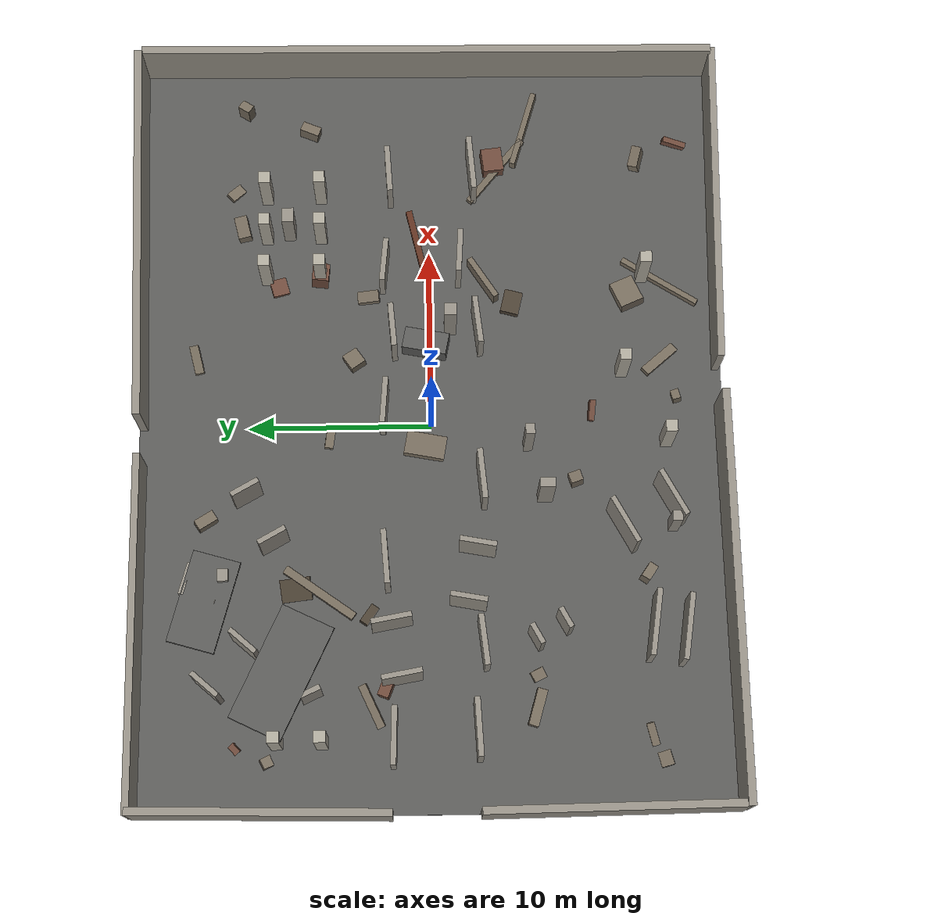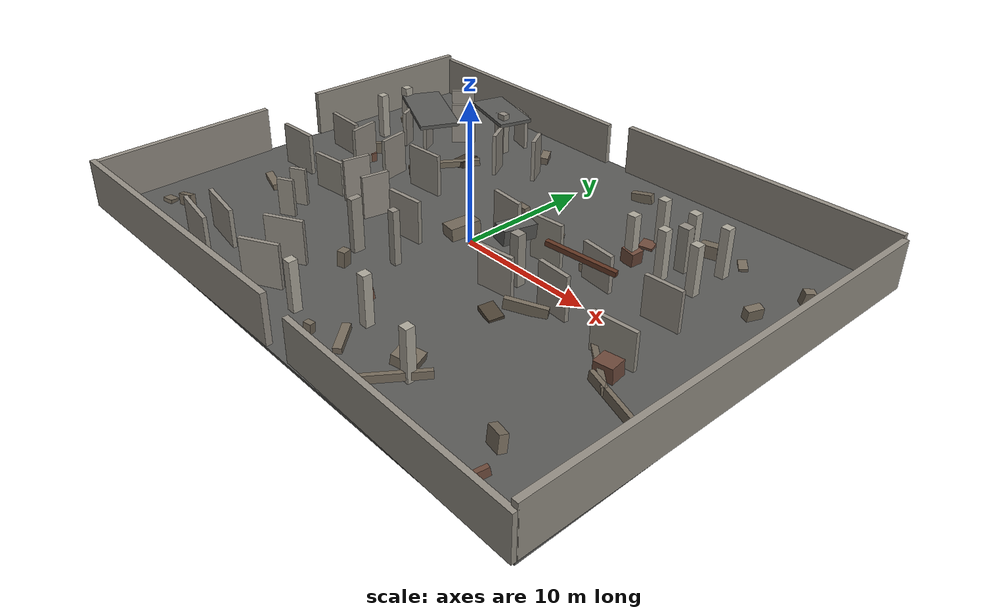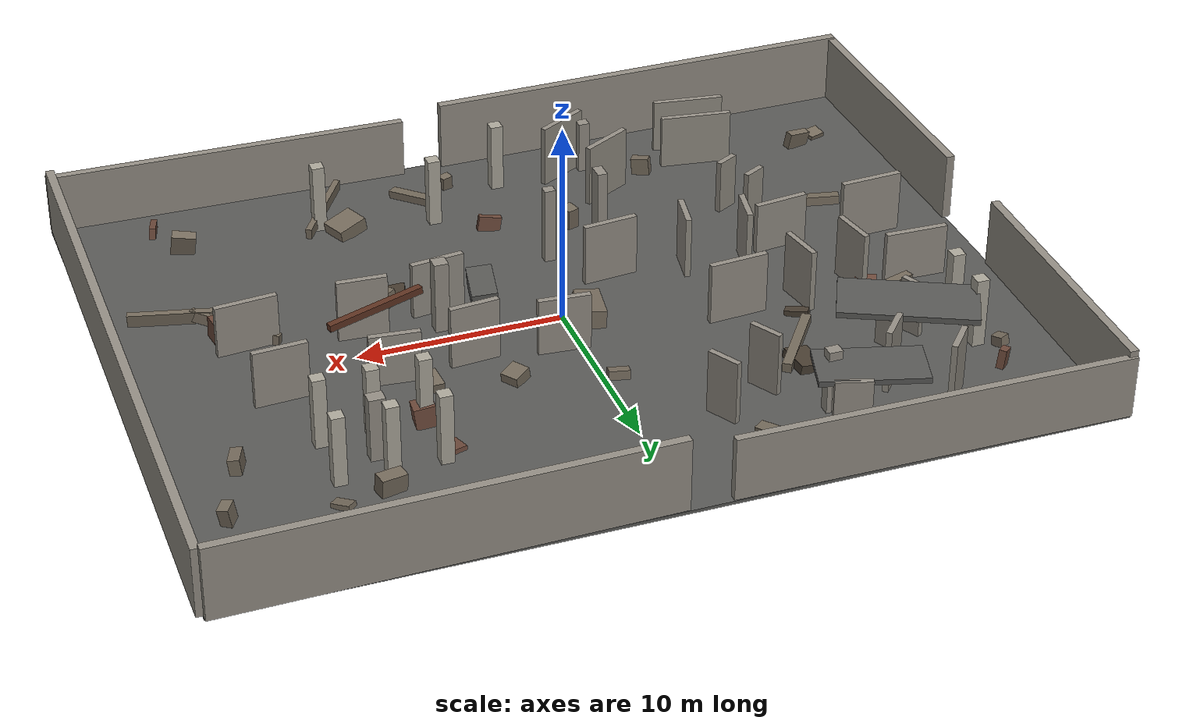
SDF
<?xml version="1.0" ?>
<sdf version="1.6">
  <model name="ruins_urban_01_base">
    <static>true</static>
    <link name="000_floor_slab">
      <pose>0.00000 0.00000 -0.08000 0.00000 0.00000 0.00000</pose>
      <visual name="visual">
        <geometry>
          <box><size>42.00000 32.00000 0.16000</size></box>
        </geometry>
          <material>
            <ambient>0.350 0.350 0.340 1</ambient>
            <diffuse>0.350 0.350 0.340 1</diffuse>
            <specular>0.03 0.03 0.03 1</specular>
          </material>
      </visual>
      <collision name="collision">
        <geometry>
          <box><size>42.00000 32.00000 0.16000</size></box>
        </geometry>
        <surface>
          <contact><collide_bitmask>0x01</collide_bitmask></contact>
          <friction>
            <ode><mu>1.0</mu><mu2>1.0</mu2></ode>
          </friction>
        </surface>
      </collision>
    </link>
    <link name="001_north_boundary_west">
      <pose>-11.50000 15.85000 1.55000 0.00000 0.00000 -0.01000</pose>
      <visual name="visual">
        <geometry>
          <box><size>19.00000 0.38000 3.10000</size></box>
        </geometry>
          <material>
            <ambient>0.580 0.560 0.520 1</ambient>
            <diffuse>0.580 0.560 0.520 1</diffuse>
            <specular>0.03 0.03 0.03 1</specular>
          </material>
      </visual>
      <collision name="collision">
        <geometry>
          <box><size>19.00000 0.38000 3.10000</size></box>
        </geometry>
        <surface>
          <contact><collide_bitmask>0x01</collide_bitmask></contact>
          <friction>
            <ode><mu>1.0</mu><mu2>1.0</mu2></ode>
          </friction>
        </surface>
      </collision>
    </link>
    <link name="002_north_boundary_east">
      <pose>10.50000 15.90000 1.80000 0.00000 0.00000 0.01500</pose>
      <visual name="visual">
        <geometry>
          <box><size>21.00000 0.42000 3.60000</size></box>
        </geometry>
          <material>
            <ambient>0.580 0.560 0.520 1</ambient>
            <diffuse>0.580 0.560 0.520 1</diffuse>
            <specular>0.03 0.03 0.03 1</specular>
          </material>
      </visual>
      <collision name="collision">
        <geometry>
          <box><size>21.00000 0.42000 3.60000</size></box>
        </geometry>
        <surface>
          <contact><collide_bitmask>0x01</collide_bitmask></contact>
          <friction>
            <ode><mu>1.0</mu><mu2>1.0</mu2></ode>
          </friction>
        </surface>
      </collision>
    </link>
    <link name="003_south_boundary_west">
      <pose>-10.00000 -15.90000 1.75000 0.00000 0.00000 0.01200</pose>
      <visual name="visual">
        <geometry>
          <box><size>22.00000 0.42000 3.50000</size></box>
        </geometry>
          <material>
            <ambient>0.580 0.560 0.520 1</ambient>
            <diffuse>0.580 0.560 0.520 1</diffuse>
            <specular>0.03 0.03 0.03 1</specular>
          </material>
      </visual>
      <collision name="collision">
        <geometry>
          <box><size>22.00000 0.42000 3.50000</size></box>
        </geometry>
        <surface>
          <contact><collide_bitmask>0x01</collide_bitmask></contact>
          <friction>
            <ode><mu>1.0</mu><mu2>1.0</mu2></ode>
          </friction>
        </surface>
      </collision>
    </link>
    <link name="004_south_boundary_east">
      <pose>12.00000 -15.85000 1.50000 0.00000 0.00000 -0.01800</pose>
      <visual name="visual">
        <geometry>
          <box><size>18.00000 0.38000 3.00000</size></box>
        </geometry>
          <material>
            <ambient>0.580 0.560 0.520 1</ambient>
            <diffuse>0.580 0.560 0.520 1</diffuse>
            <specular>0.03 0.03 0.03 1</specular>
          </material>
      </visual>
      <collision name="collision">
        <geometry>
          <box><size>18.00000 0.38000 3.00000</size></box>
        </geometry>
        <surface>
          <contact><collide_bitmask>0x01</collide_bitmask></contact>
          <friction>
            <ode><mu>1.0</mu><mu2>1.0</mu2></ode>
          </friction>
        </surface>
      </collision>
    </link>
    <link name="005_west_boundary_north">
      <pose>-20.95000 9.15000 1.70000 0.00000 0.00000 -0.02000</pose>
      <visual name="visual">
        <geometry>
          <box><size>0.42000 13.70000 3.40000</size></box>
        </geometry>
          <material>
            <ambient>0.580 0.560 0.520 1</ambient>
            <diffuse>0.580 0.560 0.520 1</diffuse>
            <specular>0.03 0.03 0.03 1</specular>
          </material>
      </visual>
      <collision name="collision">
        <geometry>
          <box><size>0.42000 13.70000 3.40000</size></box>
        </geometry>
        <surface>
          <contact><collide_bitmask>0x01</collide_bitmask></contact>
          <friction>
            <ode><mu>1.0</mu><mu2>1.0</mu2></ode>
          </friction>
        </surface>
      </collision>
    </link>
    <link name="006_west_boundary_south">
      <pose>-20.95000 -9.15000 1.70000 0.00000 0.00000 0.01500</pose>
      <visual name="visual">
        <geometry>
          <box><size>0.42000 13.70000 3.40000</size></box>
        </geometry>
          <material>
            <ambient>0.580 0.560 0.520 1</ambient>
            <diffuse>0.580 0.560 0.520 1</diffuse>
            <specular>0.03 0.03 0.03 1</specular>
          </material>
      </visual>
      <collision name="collision">
        <geometry>
          <box><size>0.42000 13.70000 3.40000</size></box>
        </geometry>
        <surface>
          <contact><collide_bitmask>0x01</collide_bitmask></contact>
          <friction>
            <ode><mu>1.0</mu><mu2>1.0</mu2></ode>
          </friction>
        </surface>
      </collision>
    </link>
    <link name="007_east_boundary">
      <pose>20.95000 0.00000 1.70000 0.00000 0.00000 -0.01000</pose>
      <visual name="visual">
        <geometry>
          <box><size>0.42000 31.80000 3.40000</size></box>
        </geometry>
          <material>
            <ambient>0.580 0.560 0.520 1</ambient>
            <diffuse>0.580 0.560 0.520 1</diffuse>
            <specular>0.03 0.03 0.03 1</specular>
          </material>
      </visual>
      <collision name="collision">
        <geometry>
          <box><size>0.42000 31.80000 3.40000</size></box>
        </geometry>
        <surface>
          <contact><collide_bitmask>0x01</collide_bitmask></contact>
          <friction>
            <ode><mu>1.0</mu><mu2>1.0</mu2></ode>
          </friction>
        </surface>
      </collision>
    </link>
    <link name="008_ground_corridor_g2_n1_left">
      <pose>-13.96680 1.73807 1.57500 0.00000 0.00000 1.74751</pose>
      <visual name="visual">
        <geometry>
          <box><size>2.18859 0.28000 3.15000</size></box>
        </geometry>
          <material>
            <ambient>0.580 0.560 0.520 1</ambient>
            <diffuse>0.580 0.560 0.520 1</diffuse>
            <specular>0.03 0.03 0.03 1</specular>
          </material>
      </visual>
      <collision name="collision">
        <geometry>
          <box><size>2.18859 0.28000 3.15000</size></box>
        </geometry>
        <surface>
          <contact><collide_bitmask>0x01</collide_bitmask></contact>
          <friction>
            <ode><mu>1.0</mu><mu2>1.0</mu2></ode>
          </friction>
        </surface>
      </collision>
    </link>
    <link name="009_ground_corridor_g2_n1_right">
      <pose>-11.03320 2.26193 1.57500 0.00000 0.00000 1.74751</pose>
      <visual name="visual">
        <geometry>
          <box><size>2.18859 0.28000 3.15000</size></box>
        </geometry>
          <material>
            <ambient>0.580 0.560 0.520 1</ambient>
            <diffuse>0.580 0.560 0.520 1</diffuse>
            <specular>0.03 0.03 0.03 1</specular>
          </material>
      </visual>
      <collision name="collision">
        <geometry>
          <box><size>2.18859 0.28000 3.15000</size></box>
        </geometry>
        <surface>
          <contact><collide_bitmask>0x01</collide_bitmask></contact>
          <friction>
            <ode><mu>1.0</mu><mu2>1.0</mu2></ode>
          </friction>
        </surface>
      </collision>
    </link>
    <link name="010_ground_corridor_n1_n2_left">
      <pose>-14.78097 6.52811 1.37500 0.00000 0.00000 2.01522</pose>
      <visual name="visual">
        <geometry>
          <box><size>1.15188 0.28000 2.75000</size></box>
        </geometry>
          <material>
            <ambient>0.580 0.560 0.520 1</ambient>
            <diffuse>0.580 0.560 0.520 1</diffuse>
            <specular>0.03 0.03 0.03 1</specular>
          </material>
      </visual>
      <collision name="collision">
        <geometry>
          <box><size>1.15188 0.28000 2.75000</size></box>
        </geometry>
        <surface>
          <contact><collide_bitmask>0x01</collide_bitmask></contact>
          <friction>
            <ode><mu>1.0</mu><mu2>1.0</mu2></ode>
          </friction>
        </surface>
      </collision>
    </link>
    <link name="011_ground_corridor_n1_n2_right">
      <pose>-13.21903 7.27189 1.37500 0.00000 0.00000 2.01522</pose>
      <visual name="visual">
        <geometry>
          <box><size>1.15188 0.28000 2.75000</size></box>
        </geometry>
          <material>
            <ambient>0.580 0.560 0.520 1</ambient>
            <diffuse>0.580 0.560 0.520 1</diffuse>
            <specular>0.03 0.03 0.03 1</specular>
          </material>
      </visual>
      <collision name="collision">
        <geometry>
          <box><size>1.15188 0.28000 2.75000</size></box>
        </geometry>
        <surface>
          <contact><collide_bitmask>0x01</collide_bitmask></contact>
          <friction>
            <ode><mu>1.0</mu><mu2>1.0</mu2></ode>
          </friction>
        </surface>
      </collision>
    </link>
    <link name="012_ground_corridor_n2_n3_left">
      <pose>-14.37134 11.98117 1.57500 0.00000 0.00000 0.85197</pose>
      <visual name="visual">
        <geometry>
          <box><size>1.81507 0.28000 3.15000</size></box>
        </geometry>
          <material>
            <ambient>0.580 0.560 0.520 1</ambient>
            <diffuse>0.580 0.560 0.520 1</diffuse>
            <specular>0.03 0.03 0.03 1</specular>
          </material>
      </visual>
      <collision name="collision">
        <geometry>
          <box><size>1.81507 0.28000 3.15000</size></box>
        </geometry>
        <surface>
          <contact><collide_bitmask>0x01</collide_bitmask></contact>
          <friction>
            <ode><mu>1.0</mu><mu2>1.0</mu2></ode>
          </friction>
        </surface>
      </collision>
    </link>
    <link name="013_ground_corridor_n2_n3_right">
      <pose>-12.12866 10.01883 1.57500 0.00000 0.00000 0.85197</pose>
      <visual name="visual">
        <geometry>
          <box><size>1.81507 0.28000 3.15000</size></box>
        </geometry>
          <material>
            <ambient>0.580 0.560 0.520 1</ambient>
            <diffuse>0.580 0.560 0.520 1</diffuse>
            <specular>0.03 0.03 0.03 1</specular>
          </material>
      </visual>
      <collision name="collision">
        <geometry>
          <box><size>1.81507 0.28000 3.15000</size></box>
        </geometry>
        <surface>
          <contact><collide_bitmask>0x01</collide_bitmask></contact>
          <friction>
            <ode><mu>1.0</mu><mu2>1.0</mu2></ode>
          </friction>
        </surface>
      </collision>
    </link>
    <link name="014_ground_corridor_n3_n4_left">
      <pose>-8.75144 13.07852 1.37500 0.00000 0.00000 -0.29146</pose>
      <visual name="visual">
        <geometry>
          <box><size>1.72015 0.28000 2.75000</size></box>
        </geometry>
          <material>
            <ambient>0.580 0.560 0.520 1</ambient>
            <diffuse>0.580 0.560 0.520 1</diffuse>
            <specular>0.03 0.03 0.03 1</specular>
          </material>
      </visual>
      <collision name="collision">
        <geometry>
          <box><size>1.72015 0.28000 2.75000</size></box>
        </geometry>
        <surface>
          <contact><collide_bitmask>0x01</collide_bitmask></contact>
          <friction>
            <ode><mu>1.0</mu><mu2>1.0</mu2></ode>
          </friction>
        </surface>
      </collision>
    </link>
    <link name="015_ground_corridor_n3_n4_right">
      <pose>-9.24856 11.42148 1.37500 0.00000 0.00000 -0.29146</pose>
      <visual name="visual">
        <geometry>
          <box><size>1.72015 0.28000 2.75000</size></box>
        </geometry>
          <material>
            <ambient>0.580 0.560 0.520 1</ambient>
            <diffuse>0.580 0.560 0.520 1</diffuse>
            <specular>0.03 0.03 0.03 1</specular>
          </material>
      </visual>
      <collision name="collision">
        <geometry>
          <box><size>1.72015 0.28000 2.75000</size></box>
        </geometry>
        <surface>
          <contact><collide_bitmask>0x01</collide_bitmask></contact>
          <friction>
            <ode><mu>1.0</mu><mu2>1.0</mu2></ode>
          </friction>
        </surface>
      </collision>
    </link>
    <link name="016_ground_corridor_n4_n5_left">
      <pose>-3.94751 9.97361 1.57500 0.00000 0.00000 -1.06370</pose>
      <visual name="visual">
        <geometry>
          <box><size>1.64782 0.28000 3.15000</size></box>
        </geometry>
          <material>
            <ambient>0.580 0.560 0.520 1</ambient>
            <diffuse>0.580 0.560 0.520 1</diffuse>
            <specular>0.03 0.03 0.03 1</specular>
          </material>
      </visual>
      <collision name="collision">
        <geometry>
          <box><size>1.64782 0.28000 3.15000</size></box>
        </geometry>
        <surface>
          <contact><collide_bitmask>0x01</collide_bitmask></contact>
          <friction>
            <ode><mu>1.0</mu><mu2>1.0</mu2></ode>
          </friction>
        </surface>
      </collision>
    </link>
    <link name="017_ground_corridor_n4_n5_right">
      <pose>-6.55249 8.52639 1.57500 0.00000 0.00000 -1.06370</pose>
      <visual name="visual">
        <geometry>
          <box><size>1.64782 0.28000 3.15000</size></box>
        </geometry>
          <material>
            <ambient>0.580 0.560 0.520 1</ambient>
            <diffuse>0.580 0.560 0.520 1</diffuse>
            <specular>0.03 0.03 0.03 1</specular>
          </material>
      </visual>
      <collision name="collision">
        <geometry>
          <box><size>1.64782 0.28000 3.15000</size></box>
        </geometry>
        <surface>
          <contact><collide_bitmask>0x01</collide_bitmask></contact>
          <friction>
            <ode><mu>1.0</mu><mu2>1.0</mu2></ode>
          </friction>
        </surface>
      </collision>
    </link>
    <link name="018_ground_corridor_g3_s1_left">
      <pose>-7.03491 -2.37131 1.57500 0.00000 0.00000 -1.75391</pose>
      <visual name="visual">
        <geometry>
          <box><size>1.99181 0.28000 3.15000</size></box>
        </geometry>
          <material>
            <ambient>0.580 0.560 0.520 1</ambient>
            <diffuse>0.580 0.560 0.520 1</diffuse>
            <specular>0.03 0.03 0.03 1</specular>
          </material>
      </visual>
      <collision name="collision">
        <geometry>
          <box><size>1.99181 0.28000 3.15000</size></box>
        </geometry>
        <surface>
          <contact><collide_bitmask>0x01</collide_bitmask></contact>
          <friction>
            <ode><mu>1.0</mu><mu2>1.0</mu2></ode>
          </friction>
        </surface>
      </collision>
    </link>
    <link name="019_ground_corridor_g3_s1_right">
      <pose>-9.96509 -1.82869 1.57500 0.00000 0.00000 -1.75391</pose>
      <visual name="visual">
        <geometry>
          <box><size>1.99181 0.28000 3.15000</size></box>
        </geometry>
          <material>
            <ambient>0.580 0.560 0.520 1</ambient>
            <diffuse>0.580 0.560 0.520 1</diffuse>
            <specular>0.03 0.03 0.03 1</specular>
          </material>
      </visual>
      <collision name="collision">
        <geometry>
          <box><size>1.99181 0.28000 3.15000</size></box>
        </geometry>
        <surface>
          <contact><collide_bitmask>0x01</collide_bitmask></contact>
          <friction>
            <ode><mu>1.0</mu><mu2>1.0</mu2></ode>
          </friction>
        </surface>
      </collision>
    </link>
    <link name="020_ground_corridor_s1_s2_left">
      <pose>-11.08900 -6.91112 1.37500 0.00000 0.00000 -2.64646</pose>
      <visual name="visual">
        <geometry>
          <box><size>1.18243 0.28000 2.75000</size></box>
        </geometry>
          <material>
            <ambient>0.580 0.560 0.520 1</ambient>
            <diffuse>0.580 0.560 0.520 1</diffuse>
            <specular>0.03 0.03 0.03 1</specular>
          </material>
      </visual>
      <collision name="collision">
        <geometry>
          <box><size>1.18243 0.28000 2.75000</size></box>
        </geometry>
        <surface>
          <contact><collide_bitmask>0x01</collide_bitmask></contact>
          <friction>
            <ode><mu>1.0</mu><mu2>1.0</mu2></ode>
          </friction>
        </surface>
      </collision>
    </link>
    <link name="021_ground_corridor_s1_s2_right">
      <pose>-11.91100 -5.38888 1.37500 0.00000 0.00000 -2.64646</pose>
      <visual name="visual">
        <geometry>
          <box><size>1.18243 0.28000 2.75000</size></box>
        </geometry>
          <material>
            <ambient>0.580 0.560 0.520 1</ambient>
            <diffuse>0.580 0.560 0.520 1</diffuse>
            <specular>0.03 0.03 0.03 1</specular>
          </material>
      </visual>
      <collision name="collision">
        <geometry>
          <box><size>1.18243 0.28000 2.75000</size></box>
        </geometry>
        <surface>
          <contact><collide_bitmask>0x01</collide_bitmask></contact>
          <friction>
            <ode><mu>1.0</mu><mu2>1.0</mu2></ode>
          </friction>
        </surface>
      </collision>
    </link>
    <link name="022_ground_corridor_s3_s4_left">
      <pose>-11.37767 -11.64369 1.37500 0.00000 0.00000 -0.14190</pose>
      <visual name="visual">
        <geometry>
          <box><size>3.57107 0.28000 2.75000</size></box>
        </geometry>
          <material>
            <ambient>0.580 0.560 0.520 1</ambient>
            <diffuse>0.580 0.560 0.520 1</diffuse>
            <specular>0.03 0.03 0.03 1</specular>
          </material>
      </visual>
      <collision name="collision">
        <geometry>
          <box><size>3.57107 0.28000 2.75000</size></box>
        </geometry>
        <surface>
          <contact><collide_bitmask>0x01</collide_bitmask></contact>
          <friction>
            <ode><mu>1.0</mu><mu2>1.0</mu2></ode>
          </friction>
        </surface>
      </collision>
    </link>
    <link name="023_ground_corridor_s3_s4_right">
      <pose>-11.62233 -13.35631 1.37500 0.00000 0.00000 -0.14190</pose>
      <visual name="visual">
        <geometry>
          <box><size>3.57107 0.28000 2.75000</size></box>
        </geometry>
          <material>
            <ambient>0.580 0.560 0.520 1</ambient>
            <diffuse>0.580 0.560 0.520 1</diffuse>
            <specular>0.03 0.03 0.03 1</specular>
          </material>
      </visual>
      <collision name="collision">
        <geometry>
          <box><size>3.57107 0.28000 2.75000</size></box>
        </geometry>
        <surface>
          <contact><collide_bitmask>0x01</collide_bitmask></contact>
          <friction>
            <ode><mu>1.0</mu><mu2>1.0</mu2></ode>
          </friction>
        </surface>
      </collision>
    </link>
    <link name="024_ground_corridor_s4_s5_left">
      <pose>-5.96349 -10.19194 1.57500 0.00000 0.00000 0.49935</pose>
      <visual name="visual">
        <geometry>
          <box><size>2.76498 0.28000 3.15000</size></box>
        </geometry>
          <material>
            <ambient>0.580 0.560 0.520 1</ambient>
            <diffuse>0.580 0.560 0.520 1</diffuse>
            <specular>0.03 0.03 0.03 1</specular>
          </material>
      </visual>
      <collision name="collision">
        <geometry>
          <box><size>2.76498 0.28000 3.15000</size></box>
        </geometry>
        <surface>
          <contact><collide_bitmask>0x01</collide_bitmask></contact>
          <friction>
            <ode><mu>1.0</mu><mu2>1.0</mu2></ode>
          </friction>
        </surface>
      </collision>
    </link>
    <link name="025_ground_corridor_s4_s5_right">
      <pose>-4.53651 -12.80806 1.57500 0.00000 0.00000 0.49935</pose>
      <visual name="visual">
        <geometry>
          <box><size>2.76498 0.28000 3.15000</size></box>
        </geometry>
          <material>
            <ambient>0.580 0.560 0.520 1</ambient>
            <diffuse>0.580 0.560 0.520 1</diffuse>
            <specular>0.03 0.03 0.03 1</specular>
          </material>
      </visual>
      <collision name="collision">
        <geometry>
          <box><size>2.76498 0.28000 3.15000</size></box>
        </geometry>
        <surface>
          <contact><collide_bitmask>0x01</collide_bitmask></contact>
          <friction>
            <ode><mu>1.0</mu><mu2>1.0</mu2></ode>
          </friction>
        </surface>
      </collision>
    </link>
    <link name="026_spine_broken_panel_00">
      <pose>-17.05000 2.20000 1.30000 0.00000 0.00000 -0.03225</pose>
      <visual name="visual">
        <geometry>
          <box><size>3.10161 0.30000 2.60000</size></box>
        </geometry>
          <material>
            <ambient>0.580 0.560 0.520 1</ambient>
            <diffuse>0.580 0.560 0.520 1</diffuse>
            <specular>0.03 0.03 0.03 1</specular>
          </material>
      </visual>
      <collision name="collision">
        <geometry>
          <box><size>3.10161 0.30000 2.60000</size></box>
        </geometry>
        <surface>
          <contact><collide_bitmask>0x01</collide_bitmask></contact>
          <friction>
            <ode><mu>1.0</mu><mu2>1.0</mu2></ode>
          </friction>
        </surface>
      </collision>
    </link>
    <link name="027_spine_broken_panel_02">
      <pose>-7.75000 2.55000 1.55000 0.00000 0.00000 0.06886</pose>
      <visual name="visual">
        <geometry>
          <box><size>2.90689 0.30000 3.10000</size></box>
        </geometry>
          <material>
            <ambient>0.580 0.560 0.520 1</ambient>
            <diffuse>0.580 0.560 0.520 1</diffuse>
            <specular>0.03 0.03 0.03 1</specular>
          </material>
      </visual>
      <collision name="collision">
        <geometry>
          <box><size>2.90689 0.30000 3.10000</size></box>
        </geometry>
        <surface>
          <contact><collide_bitmask>0x01</collide_bitmask></contact>
          <friction>
            <ode><mu>1.0</mu><mu2>1.0</mu2></ode>
          </friction>
        </surface>
      </collision>
    </link>
    <link name="028_spine_broken_panel_04">
      <pose>0.85000 2.55000 1.42500 0.00000 0.00000 -0.07983</pose>
      <visual name="visual">
        <geometry>
          <box><size>2.50799 0.30000 2.85000</size></box>
        </geometry>
          <material>
            <ambient>0.580 0.560 0.520 1</ambient>
            <diffuse>0.580 0.560 0.520 1</diffuse>
            <specular>0.03 0.03 0.03 1</specular>
          </material>
      </visual>
      <collision name="collision">
        <geometry>
          <box><size>2.50799 0.30000 2.85000</size></box>
        </geometry>
        <surface>
          <contact><collide_bitmask>0x01</collide_bitmask></contact>
          <friction>
            <ode><mu>1.0</mu><mu2>1.0</mu2></ode>
          </friction>
        </surface>
      </collision>
    </link>
    <link name="029_spine_broken_panel_05">
      <pose>5.00000 2.05000 1.55000 0.00000 0.00000 0.08314</pose>
      <visual name="visual">
        <geometry>
          <box><size>2.40832 0.30000 3.10000</size></box>
        </geometry>
          <material>
            <ambient>0.580 0.560 0.520 1</ambient>
            <diffuse>0.580 0.560 0.520 1</diffuse>
            <specular>0.03 0.03 0.03 1</specular>
          </material>
      </visual>
      <collision name="collision">
        <geometry>
          <box><size>2.40832 0.30000 3.10000</size></box>
        </geometry>
        <surface>
          <contact><collide_bitmask>0x01</collide_bitmask></contact>
          <friction>
            <ode><mu>1.0</mu><mu2>1.0</mu2></ode>
          </friction>
        </surface>
      </collision>
    </link>
    <link name="030_spine_broken_panel_06">
      <pose>8.90000 2.47500 1.30000 0.00000 0.00000 -0.10379</pose>
      <visual name="visual">
        <geometry>
          <box><size>2.41299 0.30000 2.60000</size></box>
        </geometry>
          <material>
            <ambient>0.580 0.560 0.520 1</ambient>
            <diffuse>0.580 0.560 0.520 1</diffuse>
            <specular>0.03 0.03 0.03 1</specular>
          </material>
      </visual>
      <collision name="collision">
        <geometry>
          <box><size>2.41299 0.30000 2.60000</size></box>
        </geometry>
        <surface>
          <contact><collide_bitmask>0x01</collide_bitmask></contact>
          <friction>
            <ode><mu>1.0</mu><mu2>1.0</mu2></ode>
          </friction>
        </surface>
      </collision>
    </link>
    <link name="031_spine_broken_panel_07">
      <pose>14.10000 2.17500 1.42500 0.00000 0.00000 0.05763</pose>
      <visual name="visual">
        <geometry>
          <box><size>2.60432 0.30000 2.85000</size></box>
        </geometry>
          <material>
            <ambient>0.580 0.560 0.520 1</ambient>
            <diffuse>0.580 0.560 0.520 1</diffuse>
            <specular>0.03 0.03 0.03 1</specular>
          </material>
      </visual>
      <collision name="collision">
        <geometry>
          <box><size>2.60432 0.30000 2.85000</size></box>
        </geometry>
        <surface>
          <contact><collide_bitmask>0x01</collide_bitmask></contact>
          <friction>
            <ode><mu>1.0</mu><mu2>1.0</mu2></ode>
          </friction>
        </surface>
      </collision>
    </link>
    <link name="032_spine_broken_panel_08">
      <pose>-16.75000 -2.22500 1.55000 0.00000 0.00000 0.04835</pose>
      <visual name="visual">
        <geometry>
          <box><size>3.10363 0.30000 3.10000</size></box>
        </geometry>
          <material>
            <ambient>0.580 0.560 0.520 1</ambient>
            <diffuse>0.580 0.560 0.520 1</diffuse>
            <specular>0.03 0.03 0.03 1</specular>
          </material>
      </visual>
      <collision name="collision">
        <geometry>
          <box><size>3.10363 0.30000 3.10000</size></box>
        </geometry>
        <surface>
          <contact><collide_bitmask>0x01</collide_bitmask></contact>
          <friction>
            <ode><mu>1.0</mu><mu2>1.0</mu2></ode>
          </friction>
        </surface>
      </collision>
    </link>
    <link name="033_spine_broken_panel_09">
      <pose>-12.15000 -2.60000 1.30000 0.00000 0.00000 0.11066</pose>
      <visual name="visual">
        <geometry>
          <box><size>2.71662 0.30000 2.60000</size></box>
        </geometry>
          <material>
            <ambient>0.580 0.560 0.520 1</ambient>
            <diffuse>0.580 0.560 0.520 1</diffuse>
            <specular>0.03 0.03 0.03 1</specular>
          </material>
      </visual>
      <collision name="collision">
        <geometry>
          <box><size>2.71662 0.30000 2.60000</size></box>
        </geometry>
        <surface>
          <contact><collide_bitmask>0x01</collide_bitmask></contact>
          <friction>
            <ode><mu>1.0</mu><mu2>1.0</mu2></ode>
          </friction>
        </surface>
      </collision>
    </link>
    <link name="034_spine_broken_panel_11">
      <pose>-3.35000 -2.67500 1.55000 0.00000 0.00000 0.09233</pose>
      <visual name="visual">
        <geometry>
          <box><size>2.71155 0.30000 3.10000</size></box>
        </geometry>
          <material>
            <ambient>0.580 0.560 0.520 1</ambient>
            <diffuse>0.580 0.560 0.520 1</diffuse>
            <specular>0.03 0.03 0.03 1</specular>
          </material>
      </visual>
      <collision name="collision">
        <geometry>
          <box><size>2.71155 0.30000 3.10000</size></box>
        </geometry>
        <surface>
          <contact><collide_bitmask>0x01</collide_bitmask></contact>
          <friction>
            <ode><mu>1.0</mu><mu2>1.0</mu2></ode>
          </friction>
        </surface>
      </collision>
    </link>
    <link name="035_spine_broken_panel_13">
      <pose>5.30000 -2.60000 1.42500 0.00000 0.00000 0.11488</pose>
      <visual name="visual">
        <geometry>
          <box><size>2.61725 0.30000 2.85000</size></box>
        </geometry>
          <material>
            <ambient>0.580 0.560 0.520 1</ambient>
            <diffuse>0.580 0.560 0.520 1</diffuse>
            <specular>0.03 0.03 0.03 1</specular>
          </material>
      </visual>
      <collision name="collision">
        <geometry>
          <box><size>2.61725 0.30000 2.85000</size></box>
        </geometry>
        <surface>
          <contact><collide_bitmask>0x01</collide_bitmask></contact>
          <friction>
            <ode><mu>1.0</mu><mu2>1.0</mu2></ode>
          </friction>
        </surface>
      </collision>
    </link>
    <link name="036_spine_broken_panel_14">
      <pose>9.20000 -1.67500 1.55000 0.00000 0.00000 -0.06242</pose>
      <visual name="visual">
        <geometry>
          <box><size>2.40468 0.30000 3.10000</size></box>
        </geometry>
          <material>
            <ambient>0.580 0.560 0.520 1</ambient>
            <diffuse>0.580 0.560 0.520 1</diffuse>
            <specular>0.03 0.03 0.03 1</specular>
          </material>
      </visual>
      <collision name="collision">
        <geometry>
          <box><size>2.40468 0.30000 3.10000</size></box>
        </geometry>
        <surface>
          <contact><collide_bitmask>0x01</collide_bitmask></contact>
          <friction>
            <ode><mu>1.0</mu><mu2>1.0</mu2></ode>
          </friction>
        </surface>
      </collision>
    </link>
    <link name="037_spine_broken_panel_15">
      <pose>14.50000 -2.42500 1.30000 0.00000 0.00000 0.08314</pose>
      <visual name="visual">
        <geometry>
          <box><size>3.01040 0.30000 2.60000</size></box>
        </geometry>
          <material>
            <ambient>0.580 0.560 0.520 1</ambient>
            <diffuse>0.580 0.560 0.520 1</diffuse>
            <specular>0.03 0.03 0.03 1</specular>
          </material>
      </visual>
      <collision name="collision">
        <geometry>
          <box><size>3.01040 0.30000 2.60000</size></box>
        </geometry>
        <surface>
          <contact><collide_bitmask>0x01</collide_bitmask></contact>
          <friction>
            <ode><mu>1.0</mu><mu2>1.0</mu2></ode>
          </friction>
        </surface>
      </collision>
    </link>
    <link name="038_utility_ceiling_01">
      <pose>-13.80000 8.00000 2.72000 0.00000 0.00000 -0.45000</pose>
      <visual name="visual">
        <geometry>
          <box><size>6.50000 3.00000 0.28000</size></box>
        </geometry>
          <material>
            <ambient>0.350 0.350 0.340 1</ambient>
            <diffuse>0.350 0.350 0.340 1</diffuse>
            <specular>0.03 0.03 0.03 1</specular>
          </material>
      </visual>
      <collision name="collision">
        <geometry>
          <box><size>6.50000 3.00000 0.28000</size></box>
        </geometry>
        <surface>
          <contact><collide_bitmask>0x01</collide_bitmask></contact>
          <friction>
            <ode><mu>1.0</mu><mu2>1.0</mu2></ode>
          </friction>
        </surface>
      </collision>
    </link>
    <link name="039_utility_ceiling_02">
      <pose>-10.00000 12.10000 2.62000 0.00000 0.00000 -0.28000</pose>
      <visual name="visual">
        <geometry>
          <box><size>5.00000 2.60000 0.26000</size></box>
        </geometry>
          <material>
            <ambient>0.350 0.350 0.340 1</ambient>
            <diffuse>0.350 0.350 0.340 1</diffuse>
            <specular>0.03 0.03 0.03 1</specular>
          </material>
      </visual>
      <collision name="collision">
        <geometry>
          <box><size>5.00000 2.60000 0.26000</size></box>
        </geometry>
        <surface>
          <contact><collide_bitmask>0x01</collide_bitmask></contact>
          <friction>
            <ode><mu>1.0</mu><mu2>1.0</mu2></ode>
          </friction>
        </surface>
      </collision>
    </link>
    <link name="040_fixed_column_00">
      <pose>-17.20000 6.00000 1.75000 0.00000 0.00000 0.00000</pose>
      <visual name="visual">
        <geometry>
          <box><size>0.62000 0.62000 3.50000</size></box>
        </geometry>
          <material>
            <ambient>0.680 0.660 0.610 1</ambient>
            <diffuse>0.680 0.660 0.610 1</diffuse>
            <specular>0.03 0.03 0.03 1</specular>
          </material>
      </visual>
      <collision name="collision">
        <geometry>
          <box><size>0.62000 0.62000 3.50000</size></box>
        </geometry>
        <surface>
          <contact><collide_bitmask>0x01</collide_bitmask></contact>
          <friction>
            <ode><mu>1.0</mu><mu2>1.0</mu2></ode>
          </friction>
        </surface>
      </collision>
    </link>
    <link name="041_fixed_column_01">
      <pose>-17.20000 8.40000 1.75000 0.00000 0.00000 0.00000</pose>
      <visual name="visual">
        <geometry>
          <box><size>0.62000 0.62000 3.50000</size></box>
        </geometry>
          <material>
            <ambient>0.680 0.660 0.610 1</ambient>
            <diffuse>0.680 0.660 0.610 1</diffuse>
            <specular>0.03 0.03 0.03 1</specular>
          </material>
      </visual>
      <collision name="collision">
        <geometry>
          <box><size>0.62000 0.62000 3.50000</size></box>
        </geometry>
        <surface>
          <contact><collide_bitmask>0x01</collide_bitmask></contact>
          <friction>
            <ode><mu>1.0</mu><mu2>1.0</mu2></ode>
          </friction>
        </surface>
      </collision>
    </link>
    <link name="042_fixed_column_03">
      <pose>8.60000 6.00000 1.75000 0.00000 0.00000 0.00000</pose>
      <visual name="visual">
        <geometry>
          <box><size>0.62000 0.62000 3.50000</size></box>
        </geometry>
          <material>
            <ambient>0.680 0.660 0.610 1</ambient>
            <diffuse>0.680 0.660 0.610 1</diffuse>
            <specular>0.03 0.03 0.03 1</specular>
          </material>
      </visual>
      <collision name="collision">
        <geometry>
          <box><size>0.62000 0.62000 3.50000</size></box>
        </geometry>
        <surface>
          <contact><collide_bitmask>0x01</collide_bitmask></contact>
          <friction>
            <ode><mu>1.0</mu><mu2>1.0</mu2></ode>
          </friction>
        </surface>
      </collision>
    </link>
    <link name="043_fixed_column_04">
      <pose>11.00000 6.00000 1.75000 0.00000 0.00000 0.00000</pose>
      <visual name="visual">
        <geometry>
          <box><size>0.62000 0.62000 3.50000</size></box>
        </geometry>
          <material>
            <ambient>0.680 0.660 0.610 1</ambient>
            <diffuse>0.680 0.660 0.610 1</diffuse>
            <specular>0.03 0.03 0.03 1</specular>
          </material>
      </visual>
      <collision name="collision">
        <geometry>
          <box><size>0.62000 0.62000 3.50000</size></box>
        </geometry>
        <surface>
          <contact><collide_bitmask>0x01</collide_bitmask></contact>
          <friction>
            <ode><mu>1.0</mu><mu2>1.0</mu2></ode>
          </friction>
        </surface>
      </collision>
    </link>
    <link name="044_fixed_column_05">
      <pose>13.40000 6.00000 1.75000 0.00000 0.00000 0.00000</pose>
      <visual name="visual">
        <geometry>
          <box><size>0.62000 0.62000 3.50000</size></box>
        </geometry>
          <material>
            <ambient>0.680 0.660 0.610 1</ambient>
            <diffuse>0.680 0.660 0.610 1</diffuse>
            <specular>0.03 0.03 0.03 1</specular>
          </material>
      </visual>
      <collision name="collision">
        <geometry>
          <box><size>0.62000 0.62000 3.50000</size></box>
        </geometry>
        <surface>
          <contact><collide_bitmask>0x01</collide_bitmask></contact>
          <friction>
            <ode><mu>1.0</mu><mu2>1.0</mu2></ode>
          </friction>
        </surface>
      </collision>
    </link>
    <link name="045_fixed_column_06">
      <pose>8.60000 9.00000 1.75000 0.00000 0.00000 0.00000</pose>
      <visual name="visual">
        <geometry>
          <box><size>0.62000 0.62000 3.50000</size></box>
        </geometry>
          <material>
            <ambient>0.680 0.660 0.610 1</ambient>
            <diffuse>0.680 0.660 0.610 1</diffuse>
            <specular>0.03 0.03 0.03 1</specular>
          </material>
      </visual>
      <collision name="collision">
        <geometry>
          <box><size>0.62000 0.62000 3.50000</size></box>
        </geometry>
        <surface>
          <contact><collide_bitmask>0x01</collide_bitmask></contact>
          <friction>
            <ode><mu>1.0</mu><mu2>1.0</mu2></ode>
          </friction>
        </surface>
      </collision>
    </link>
    <link name="046_fixed_column_07">
      <pose>11.00000 9.00000 1.75000 0.00000 0.00000 0.00000</pose>
      <visual name="visual">
        <geometry>
          <box><size>0.62000 0.62000 3.50000</size></box>
        </geometry>
          <material>
            <ambient>0.680 0.660 0.610 1</ambient>
            <diffuse>0.680 0.660 0.610 1</diffuse>
            <specular>0.03 0.03 0.03 1</specular>
          </material>
      </visual>
      <collision name="collision">
        <geometry>
          <box><size>0.62000 0.62000 3.50000</size></box>
        </geometry>
        <surface>
          <contact><collide_bitmask>0x01</collide_bitmask></contact>
          <friction>
            <ode><mu>1.0</mu><mu2>1.0</mu2></ode>
          </friction>
        </surface>
      </collision>
    </link>
    <link name="047_fixed_column_08">
      <pose>13.40000 9.00000 1.75000 0.00000 0.00000 0.00000</pose>
      <visual name="visual">
        <geometry>
          <box><size>0.62000 0.62000 3.50000</size></box>
        </geometry>
          <material>
            <ambient>0.680 0.660 0.610 1</ambient>
            <diffuse>0.680 0.660 0.610 1</diffuse>
            <specular>0.03 0.03 0.03 1</specular>
          </material>
      </visual>
      <collision name="collision">
        <geometry>
          <box><size>0.62000 0.62000 3.50000</size></box>
        </geometry>
        <surface>
          <contact><collide_bitmask>0x01</collide_bitmask></contact>
          <friction>
            <ode><mu>1.0</mu><mu2>1.0</mu2></ode>
          </friction>
        </surface>
      </collision>
    </link>
    <link name="048_fixed_column_09">
      <pose>-1.00000 -12.80000 1.75000 0.00000 0.00000 0.00000</pose>
      <visual name="visual">
        <geometry>
          <box><size>0.62000 0.62000 3.50000</size></box>
        </geometry>
          <material>
            <ambient>0.680 0.660 0.610 1</ambient>
            <diffuse>0.680 0.660 0.610 1</diffuse>
            <specular>0.03 0.03 0.03 1</specular>
          </material>
      </visual>
      <collision name="collision">
        <geometry>
          <box><size>0.62000 0.62000 3.50000</size></box>
        </geometry>
        <surface>
          <contact><collide_bitmask>0x01</collide_bitmask></contact>
          <friction>
            <ode><mu>1.0</mu><mu2>1.0</mu2></ode>
          </friction>
        </surface>
      </collision>
    </link>
    <link name="049_fixed_column_10">
      <pose>3.00000 -10.50000 1.75000 0.00000 0.00000 0.00000</pose>
      <visual name="visual">
        <geometry>
          <box><size>0.62000 0.62000 3.50000</size></box>
        </geometry>
          <material>
            <ambient>0.680 0.660 0.610 1</ambient>
            <diffuse>0.680 0.660 0.610 1</diffuse>
            <specular>0.03 0.03 0.03 1</specular>
          </material>
      </visual>
      <collision name="collision">
        <geometry>
          <box><size>0.62000 0.62000 3.50000</size></box>
        </geometry>
        <surface>
          <contact><collide_bitmask>0x01</collide_bitmask></contact>
          <friction>
            <ode><mu>1.0</mu><mu2>1.0</mu2></ode>
          </friction>
        </surface>
      </collision>
    </link>
    <link name="050_fixed_column_11">
      <pose>8.50000 -11.80000 1.75000 0.00000 0.00000 0.00000</pose>
      <visual name="visual">
        <geometry>
          <box><size>0.62000 0.62000 3.50000</size></box>
        </geometry>
          <material>
            <ambient>0.680 0.660 0.610 1</ambient>
            <diffuse>0.680 0.660 0.610 1</diffuse>
            <specular>0.03 0.03 0.03 1</specular>
          </material>
      </visual>
      <collision name="collision">
        <geometry>
          <box><size>0.62000 0.62000 3.50000</size></box>
        </geometry>
        <surface>
          <contact><collide_bitmask>0x01</collide_bitmask></contact>
          <friction>
            <ode><mu>1.0</mu><mu2>1.0</mu2></ode>
          </friction>
        </surface>
      </collision>
    </link>
    <link name="051_overflight_rubble_gate">
      <pose>-1.20000 0.35000 0.45000 0.05000 -0.06000 -0.18000</pose>
      <visual name="visual">
        <geometry>
          <box><size>1.25000 2.20000 0.90000</size></box>
        </geometry>
          <material>
            <ambient>0.460 0.420 0.360 1</ambient>
            <diffuse>0.460 0.420 0.360 1</diffuse>
            <specular>0.03 0.03 0.03 1</specular>
          </material>
      </visual>
      <collision name="collision">
        <geometry>
          <box><size>1.25000 2.20000 0.90000</size></box>
        </geometry>
        <surface>
          <contact><collide_bitmask>0x01</collide_bitmask></contact>
          <friction>
            <ode><mu>1.0</mu><mu2>1.0</mu2></ode>
          </friction>
        </surface>
      </collision>
    </link>
    <link name="052_underflight_hanging_gate">
      <pose>4.00000 0.25000 2.55000 -0.04000 0.08000 -0.20000</pose>
      <visual name="visual">
        <geometry>
          <box><size>1.20000 2.40000 1.05000</size></box>
        </geometry>
          <material>
            <ambient>0.350 0.350 0.340 1</ambient>
            <diffuse>0.350 0.350 0.340 1</diffuse>
            <specular>0.03 0.03 0.03 1</specular>
          </material>
      </visual>
      <collision name="collision">
        <geometry>
          <box><size>1.20000 2.40000 1.05000</size></box>
        </geometry>
        <surface>
          <contact><collide_bitmask>0x01</collide_bitmask></contact>
          <friction>
            <ode><mu>1.0</mu><mu2>1.0</mu2></ode>
          </friction>
        </surface>
      </collision>
    </link>
    <link name="053_east_slanted_beam">
      <pose>9.20000 0.55000 2.85000 0.00000 0.10000 0.22000</pose>
      <visual name="visual">
        <geometry>
          <box><size>4.80000 0.34000 0.34000</size></box>
        </geometry>
          <material>
            <ambient>0.370 0.200 0.130 1</ambient>
            <diffuse>0.370 0.200 0.130 1</diffuse>
            <specular>0.03 0.03 0.03 1</specular>
          </material>
      </visual>
      <collision name="collision">
        <geometry>
          <box><size>4.80000 0.34000 0.34000</size></box>
        </geometry>
        <surface>
          <contact><collide_bitmask>0x01</collide_bitmask></contact>
          <friction>
            <ode><mu>1.0</mu><mu2>1.0</mu2></ode>
          </friction>
        </surface>
      </collision>
    </link>
    <link name="054_base_random_column_00">
      <pose>-5.73317 -12.99629 1.33825 0.00000 0.00000 0.00000</pose>
      <visual name="visual">
        <geometry>
          <box><size>0.55366 0.53266 2.67650</size></box>
        </geometry>
          <material>
            <ambient>0.580 0.560 0.520 1</ambient>
            <diffuse>0.580 0.560 0.520 1</diffuse>
            <specular>0.03 0.03 0.03 1</specular>
          </material>
      </visual>
      <collision name="collision">
        <geometry>
          <box><size>0.55366 0.53266 2.67650</size></box>
        </geometry>
        <surface>
          <contact><collide_bitmask>0x01</collide_bitmask></contact>
          <friction>
            <ode><mu>1.0</mu><mu2>1.0</mu2></ode>
          </friction>
        </surface>
      </collision>
    </link>
    <link name="055_base_random_column_01">
      <pose>-8.65912 11.08855 1.59380 0.00000 0.00000 0.00000</pose>
      <visual name="visual">
        <geometry>
          <box><size>0.65716 0.54913 3.18760</size></box>
        </geometry>
          <material>
            <ambient>0.580 0.560 0.520 1</ambient>
            <diffuse>0.580 0.560 0.520 1</diffuse>
            <specular>0.03 0.03 0.03 1</specular>
          </material>
      </visual>
      <collision name="collision">
        <geometry>
          <box><size>0.65716 0.54913 3.18760</size></box>
        </geometry>
        <surface>
          <contact><collide_bitmask>0x01</collide_bitmask></contact>
          <friction>
            <ode><mu>1.0</mu><mu2>1.0</mu2></ode>
          </friction>
        </surface>
      </collision>
    </link>
    <link name="056_base_random_column_02">
      <pose>5.62630 -1.10804 1.81061 0.00000 0.00000 0.00000</pose>
      <visual name="visual">
        <geometry>
          <box><size>0.69136 0.66345 3.62122</size></box>
        </geometry>
          <material>
            <ambient>0.580 0.560 0.520 1</ambient>
            <diffuse>0.580 0.560 0.520 1</diffuse>
            <specular>0.03 0.03 0.03 1</specular>
          </material>
      </visual>
      <collision name="collision">
        <geometry>
          <box><size>0.69136 0.66345 3.62122</size></box>
        </geometry>
        <surface>
          <contact><collide_bitmask>0x01</collide_bitmask></contact>
          <friction>
            <ode><mu>1.0</mu><mu2>1.0</mu2></ode>
          </friction>
        </surface>
      </collision>
    </link>
    <link name="057_base_random_column_03">
      <pose>-4.09062 -6.09016 1.93482 0.00000 0.00000 0.00000</pose>
      <visual name="visual">
        <geometry>
          <box><size>0.48531 0.82253 3.86965</size></box>
        </geometry>
          <material>
            <ambient>0.580 0.560 0.520 1</ambient>
            <diffuse>0.580 0.560 0.520 1</diffuse>
            <specular>0.03 0.03 0.03 1</specular>
          </material>
      </visual>
      <collision name="collision">
        <geometry>
          <box><size>0.48531 0.82253 3.86965</size></box>
        </geometry>
        <surface>
          <contact><collide_bitmask>0x01</collide_bitmask></contact>
          <friction>
            <ode><mu>1.0</mu><mu2>1.0</mu2></ode>
          </friction>
        </surface>
      </collision>
    </link>
    <link name="058_base_random_column_04">
      <pose>11.32133 7.73776 1.57901 0.00000 0.00000 0.00000</pose>
      <visual name="visual">
        <geometry>
          <box><size>0.77641 0.64260 3.15802</size></box>
        </geometry>
          <material>
            <ambient>0.580 0.560 0.520 1</ambient>
            <diffuse>0.580 0.560 0.520 1</diffuse>
            <specular>0.03 0.03 0.03 1</specular>
          </material>
      </visual>
      <collision name="collision">
        <geometry>
          <box><size>0.77641 0.64260 3.15802</size></box>
        </geometry>
        <surface>
          <contact><collide_bitmask>0x01</collide_bitmask></contact>
          <friction>
            <ode><mu>1.0</mu><mu2>1.0</mu2></ode>
          </friction>
        </surface>
      </collision>
    </link>
    <link name="059_base_random_column_05">
      <pose>-1.16520 -5.23505 1.93866 0.00000 0.00000 0.00000</pose>
      <visual name="visual">
        <geometry>
          <box><size>0.54675 0.49649 3.87733</size></box>
        </geometry>
          <material>
            <ambient>0.580 0.560 0.520 1</ambient>
            <diffuse>0.580 0.560 0.520 1</diffuse>
            <specular>0.03 0.03 0.03 1</specular>
          </material>
      </visual>
      <collision name="collision">
        <geometry>
          <box><size>0.54675 0.49649 3.87733</size></box>
        </geometry>
        <surface>
          <contact><collide_bitmask>0x01</collide_bitmask></contact>
          <friction>
            <ode><mu>1.0</mu><mu2>1.0</mu2></ode>
          </friction>
        </surface>
      </collision>
    </link>
    <link name="060_base_rubble_000">
      <pose>0.69368 -8.77868 0.37933 -0.06838 0.17858 3.03112</pose>
      <visual name="visual">
        <geometry>
          <box><size>1.13273 0.31544 0.75866</size></box>
        </geometry>
          <material>
            <ambient>0.430 0.290 0.230 1</ambient>
            <diffuse>0.430 0.290 0.230 1</diffuse>
            <specular>0.03 0.03 0.03 1</specular>
          </material>
      </visual>
      <collision name="collision">
        <geometry>
          <box><size>1.13273 0.31544 0.75866</size></box>
        </geometry>
        <surface>
          <contact><collide_bitmask>0x01</collide_bitmask></contact>
          <friction>
            <ode><mu>1.0</mu><mu2>1.0</mu2></ode>
          </friction>
        </surface>
      </collision>
    </link>
    <link name="061_base_rubble_001">
      <pose>7.41804 3.38708 0.25396 -0.10298 -0.05295 0.09406</pose>
      <visual name="visual">
        <geometry>
          <box><size>0.64593 1.17779 0.50792</size></box>
        </geometry>
          <material>
            <ambient>0.460 0.420 0.360 1</ambient>
            <diffuse>0.460 0.420 0.360 1</diffuse>
            <specular>0.03 0.03 0.03 1</specular>
          </material>
      </visual>
      <collision name="collision">
        <geometry>
          <box><size>0.64593 1.17779 0.50792</size></box>
        </geometry>
        <surface>
          <contact><collide_bitmask>0x01</collide_bitmask></contact>
          <friction>
            <ode><mu>1.0</mu><mu2>1.0</mu2></ode>
          </friction>
        </surface>
      </collision>
    </link>
    <link name="062_base_rubble_002">
      <pose>-3.16065 -7.79097 0.54282 0.04106 0.05884 1.89598</pose>
      <visual name="visual">
        <geometry>
          <box><size>0.68196 0.59113 1.08564</size></box>
        </geometry>
          <material>
            <ambient>0.460 0.420 0.360 1</ambient>
            <diffuse>0.460 0.420 0.360 1</diffuse>
            <specular>0.03 0.03 0.03 1</specular>
          </material>
      </visual>
      <collision name="collision">
        <geometry>
          <box><size>0.68196 0.59113 1.08564</size></box>
        </geometry>
        <surface>
          <contact><collide_bitmask>0x01</collide_bitmask></contact>
          <friction>
            <ode><mu>1.0</mu><mu2>1.0</mu2></ode>
          </friction>
        </surface>
      </collision>
    </link>
    <link name="063_base_rubble_003">
      <pose>-5.20781 12.27135 0.30559 0.07202 -0.10332 2.14174</pose>
      <visual name="visual">
        <geometry>
          <box><size>1.14079 0.60545 0.61118</size></box>
        </geometry>
          <material>
            <ambient>0.460 0.420 0.360 1</ambient>
            <diffuse>0.460 0.420 0.360 1</diffuse>
            <specular>0.03 0.03 0.03 1</specular>
          </material>
      </visual>
      <collision name="collision">
        <geometry>
          <box><size>1.14079 0.60545 0.61118</size></box>
        </geometry>
        <surface>
          <contact><collide_bitmask>0x01</collide_bitmask></contact>
          <friction>
            <ode><mu>1.0</mu><mu2>1.0</mu2></ode>
          </friction>
        </surface>
      </collision>
    </link>
    <link name="064_base_rubble_004">
      <pose>-14.35665 2.58318 0.34187 0.00596 0.09389 1.19255</pose>
      <visual name="visual">
        <geometry>
          <box><size>0.61264 1.02405 0.68374</size></box>
        </geometry>
          <material>
            <ambient>0.430 0.290 0.230 1</ambient>
            <diffuse>0.430 0.290 0.230 1</diffuse>
            <specular>0.03 0.03 0.03 1</specular>
          </material>
      </visual>
      <collision name="collision">
        <geometry>
          <box><size>0.61264 1.02405 0.68374</size></box>
        </geometry>
        <surface>
          <contact><collide_bitmask>0x01</collide_bitmask></contact>
          <friction>
            <ode><mu>1.0</mu><mu2>1.0</mu2></ode>
          </friction>
        </surface>
      </collision>
    </link>
    <link name="065_base_rubble_005">
      <pose>-13.75689 -5.48803 0.21482 -0.12590 -0.01291 2.04278</pose>
      <visual name="visual">
        <geometry>
          <box><size>0.72122 0.59020 0.42964</size></box>
        </geometry>
          <material>
            <ambient>0.460 0.420 0.360 1</ambient>
            <diffuse>0.460 0.420 0.360 1</diffuse>
            <specular>0.03 0.03 0.03 1</specular>
          </material>
      </visual>
      <collision name="collision">
        <geometry>
          <box><size>0.72122 0.59020 0.42964</size></box>
        </geometry>
        <surface>
          <contact><collide_bitmask>0x01</collide_bitmask></contact>
          <friction>
            <ode><mu>1.0</mu><mu2>1.0</mu2></ode>
          </friction>
        </surface>
      </collision>
    </link>
    <link name="066_base_rubble_006">
      <pose>3.88785 12.86551 0.33204 -0.02583 -0.15363 0.22298</pose>
      <visual name="visual">
        <geometry>
          <box><size>1.57082 0.48658 0.66408</size></box>
        </geometry>
          <material>
            <ambient>0.460 0.420 0.360 1</ambient>
            <diffuse>0.460 0.420 0.360 1</diffuse>
            <specular>0.03 0.03 0.03 1</specular>
          </material>
      </visual>
      <collision name="collision">
        <geometry>
          <box><size>1.57082 0.48658 0.66408</size></box>
        </geometry>
        <surface>
          <contact><collide_bitmask>0x01</collide_bitmask></contact>
          <friction>
            <ode><mu>1.0</mu><mu2>1.0</mu2></ode>
          </friction>
        </surface>
      </collision>
    </link>
    <link name="067_base_rubble_007">
      <pose>7.01440 -4.54363 0.15774 -0.05409 -0.17481 2.90814</pose>
      <visual name="visual">
        <geometry>
          <box><size>1.38252 1.01835 0.31548</size></box>
        </geometry>
          <material>
            <ambient>0.290 0.250 0.200 1</ambient>
            <diffuse>0.290 0.250 0.200 1</diffuse>
            <specular>0.03 0.03 0.03 1</specular>
          </material>
      </visual>
      <collision name="collision">
        <geometry>
          <box><size>1.38252 1.01835 0.31548</size></box>
        </geometry>
        <surface>
          <contact><collide_bitmask>0x01</collide_bitmask></contact>
          <friction>
            <ode><mu>1.0</mu><mu2>1.0</mu2></ode>
          </friction>
        </surface>
      </collision>
    </link>
    <link name="068_base_rubble_008">
      <pose>15.25083 -3.62352 0.51768 0.03225 -0.03571 0.12304</pose>
      <visual name="visual">
        <geometry>
          <box><size>1.30734 1.13507 1.03537</size></box>
        </geometry>
          <material>
            <ambient>0.430 0.290 0.230 1</ambient>
            <diffuse>0.430 0.290 0.230 1</diffuse>
            <specular>0.03 0.03 0.03 1</specular>
          </material>
      </visual>
      <collision name="collision">
        <geometry>
          <box><size>1.30734 1.13507 1.03537</size></box>
        </geometry>
        <surface>
          <contact><collide_bitmask>0x01</collide_bitmask></contact>
          <friction>
            <ode><mu>1.0</mu><mu2>1.0</mu2></ode>
          </friction>
        </surface>
      </collision>
    </link>
    <link name="069_base_rubble_009">
      <pose>-18.19326 8.93807 0.25219 0.17750 -0.01705 0.45858</pose>
      <visual name="visual">
        <geometry>
          <box><size>0.57383 0.57875 0.50438</size></box>
        </geometry>
          <material>
            <ambient>0.460 0.420 0.360 1</ambient>
            <diffuse>0.460 0.420 0.360 1</diffuse>
            <specular>0.03 0.03 0.03 1</specular>
          </material>
      </visual>
      <collision name="collision">
        <geometry>
          <box><size>0.57383 0.57875 0.50438</size></box>
        </geometry>
        <surface>
          <contact><collide_bitmask>0x01</collide_bitmask></contact>
          <friction>
            <ode><mu>1.0</mu><mu2>1.0</mu2></ode>
          </friction>
        </surface>
      </collision>
    </link>
    <link name="070_base_rubble_010">
      <pose>17.29969 6.58739 0.39626 -0.02113 -0.12436 2.75779</pose>
      <visual name="visual">
        <geometry>
          <box><size>0.55135 1.07638 0.79253</size></box>
        </geometry>
          <material>
            <ambient>0.460 0.420 0.360 1</ambient>
            <diffuse>0.460 0.420 0.360 1</diffuse>
            <specular>0.03 0.03 0.03 1</specular>
          </material>
      </visual>
      <collision name="collision">
        <geometry>
          <box><size>0.55135 1.07638 0.79253</size></box>
        </geometry>
        <surface>
          <contact><collide_bitmask>0x01</collide_bitmask></contact>
          <friction>
            <ode><mu>1.0</mu><mu2>1.0</mu2></ode>
          </friction>
        </surface>
      </collision>
    </link>
    <link name="071_base_rubble_011">
      <pose>-8.38826 -11.54913 0.43450 -0.04643 -0.12408 2.54488</pose>
      <visual name="visual">
        <geometry>
          <box><size>0.89972 0.51508 0.86900</size></box>
        </geometry>
          <material>
            <ambient>0.460 0.420 0.360 1</ambient>
            <diffuse>0.460 0.420 0.360 1</diffuse>
            <specular>0.03 0.03 0.03 1</specular>
          </material>
      </visual>
      <collision name="collision">
        <geometry>
          <box><size>0.89972 0.51508 0.86900</size></box>
        </geometry>
        <surface>
          <contact><collide_bitmask>0x01</collide_bitmask></contact>
          <friction>
            <ode><mu>1.0</mu><mu2>1.0</mu2></ode>
          </friction>
        </surface>
      </collision>
    </link>
    <link name="072_base_rubble_012">
      <pose>-17.47175 10.60928 0.46590 -0.13339 0.06822 2.30324</pose>
      <visual name="visual">
        <geometry>
          <box><size>0.35651 0.58048 0.93179</size></box>
        </geometry>
          <material>
            <ambient>0.430 0.290 0.230 1</ambient>
            <diffuse>0.430 0.290 0.230 1</diffuse>
            <specular>0.03 0.03 0.03 1</specular>
          </material>
      </visual>
      <collision name="collision">
        <geometry>
          <box><size>0.35651 0.58048 0.93179</size></box>
        </geometry>
        <surface>
          <contact><collide_bitmask>0x01</collide_bitmask></contact>
          <friction>
            <ode><mu>1.0</mu><mu2>1.0</mu2></ode>
          </friction>
        </surface>
      </collision>
    </link>
    <link name="073_base_rubble_013">
      <pose>1.46314 -13.42751 0.36021 -0.09674 0.06898 0.26857</pose>
      <visual name="visual">
        <geometry>
          <box><size>0.54129 0.45559 0.72042</size></box>
        </geometry>
          <material>
            <ambient>0.460 0.420 0.360 1</ambient>
            <diffuse>0.460 0.420 0.360 1</diffuse>
            <specular>0.03 0.03 0.03 1</specular>
          </material>
      </visual>
      <collision name="collision">
        <geometry>
          <box><size>0.54129 0.45559 0.72042</size></box>
        </geometry>
        <surface>
          <contact><collide_bitmask>0x01</collide_bitmask></contact>
          <friction>
            <ode><mu>1.0</mu><mu2>1.0</mu2></ode>
          </friction>
        </surface>
      </collision>
    </link>
    <link name="074_base_rubble_014">
      <pose>-9.00232 7.39009 0.22118 -0.16347 0.02564 1.69424</pose>
      <visual name="visual">
        <geometry>
          <box><size>1.64263 1.23648 0.44236</size></box>
        </geometry>
          <material>
            <ambient>0.290 0.250 0.200 1</ambient>
            <diffuse>0.290 0.250 0.200 1</diffuse>
            <specular>0.03 0.03 0.03 1</specular>
          </material>
      </visual>
      <collision name="collision">
        <geometry>
          <box><size>1.64263 1.23648 0.44236</size></box>
        </geometry>
        <surface>
          <contact><collide_bitmask>0x01</collide_bitmask></contact>
          <friction>
            <ode><mu>1.0</mu><mu2>1.0</mu2></ode>
          </friction>
        </surface>
      </collision>
    </link>
    <link name="075_base_rubble_015">
      <pose>18.59276 10.20899 0.47607 0.13220 -0.12239 2.53401</pose>
      <visual name="visual">
        <geometry>
          <box><size>0.53001 0.71681 0.95215</size></box>
        </geometry>
          <material>
            <ambient>0.460 0.420 0.360 1</ambient>
            <diffuse>0.460 0.420 0.360 1</diffuse>
            <specular>0.03 0.03 0.03 1</specular>
          </material>
      </visual>
      <collision name="collision">
        <geometry>
          <box><size>0.53001 0.71681 0.95215</size></box>
        </geometry>
        <surface>
          <contact><collide_bitmask>0x01</collide_bitmask></contact>
          <friction>
            <ode><mu>1.0</mu><mu2>1.0</mu2></ode>
          </friction>
        </surface>
      </collision>
    </link>
    <link name="076_base_rubble_016">
      <pose>8.10554 8.33616 0.11115 0.09824 0.00494 0.27383</pose>
      <visual name="visual">
        <geometry>
          <box><size>0.96019 0.92242 0.22231</size></box>
        </geometry>
          <material>
            <ambient>0.430 0.290 0.230 1</ambient>
            <diffuse>0.430 0.290 0.230 1</diffuse>
            <specular>0.03 0.03 0.03 1</specular>
          </material>
      </visual>
      <collision name="collision">
        <geometry>
          <box><size>0.96019 0.92242 0.22231</size></box>
        </geometry>
        <surface>
          <contact><collide_bitmask>0x01</collide_bitmask></contact>
          <friction>
            <ode><mu>1.0</mu><mu2>1.0</mu2></ode>
          </friction>
        </surface>
      </collision>
    </link>
    <link name="077_base_rubble_017">
      <pose>-16.98840 -11.44090 0.41576 -0.11942 -0.13869 0.25775</pose>
      <visual name="visual">
        <geometry>
          <box><size>1.20735 0.41840 0.83152</size></box>
        </geometry>
          <material>
            <ambient>0.460 0.420 0.360 1</ambient>
            <diffuse>0.460 0.420 0.360 1</diffuse>
            <specular>0.03 0.03 0.03 1</specular>
          </material>
      </visual>
      <collision name="collision">
        <geometry>
          <box><size>1.20735 0.41840 0.83152</size></box>
        </geometry>
        <surface>
          <contact><collide_bitmask>0x01</collide_bitmask></contact>
          <friction>
            <ode><mu>1.0</mu><mu2>1.0</mu2></ode>
          </friction>
        </surface>
      </collision>
    </link>
    <link name="078_base_rubble_018">
      <pose>7.40315 -10.95616 0.34235 -0.00917 0.17534 0.39782</pose>
      <visual name="visual">
        <geometry>
          <box><size>1.55593 1.33416 0.68469</size></box>
        </geometry>
          <material>
            <ambient>0.460 0.420 0.360 1</ambient>
            <diffuse>0.460 0.420 0.360 1</diffuse>
            <specular>0.03 0.03 0.03 1</specular>
          </material>
      </visual>
      <collision name="collision">
        <geometry>
          <box><size>1.55593 1.33416 0.68469</size></box>
        </geometry>
        <surface>
          <contact><collide_bitmask>0x01</collide_bitmask></contact>
          <friction>
            <ode><mu>1.0</mu><mu2>1.0</mu2></ode>
          </friction>
        </surface>
      </collision>
    </link>
    <link name="079_base_rubble_019">
      <pose>-0.69200 5.55893 0.22500 -0.05298 -0.11693 1.43685</pose>
      <visual name="visual">
        <geometry>
          <box><size>0.46745 1.00889 0.44999</size></box>
        </geometry>
          <material>
            <ambient>0.460 0.420 0.360 1</ambient>
            <diffuse>0.460 0.420 0.360 1</diffuse>
            <specular>0.03 0.03 0.03 1</specular>
          </material>
      </visual>
      <collision name="collision">
        <geometry>
          <box><size>0.46745 1.00889 0.44999</size></box>
        </geometry>
        <surface>
          <contact><collide_bitmask>0x01</collide_bitmask></contact>
          <friction>
            <ode><mu>1.0</mu><mu2>1.0</mu2></ode>
          </friction>
        </surface>
      </collision>
    </link>
    <link name="080_base_rubble_020">
      <pose>16.34330 -13.95268 0.27904 -0.03087 -0.16671 1.29589</pose>
      <visual name="visual">
        <geometry>
          <box><size>1.31256 0.30755 0.55808</size></box>
        </geometry>
          <material>
            <ambient>0.430 0.290 0.230 1</ambient>
            <diffuse>0.430 0.290 0.230 1</diffuse>
            <specular>0.03 0.03 0.03 1</specular>
          </material>
      </visual>
      <collision name="collision">
        <geometry>
          <box><size>1.31256 0.30755 0.55808</size></box>
        </geometry>
        <surface>
          <contact><collide_bitmask>0x01</collide_bitmask></contact>
          <friction>
            <ode><mu>1.0</mu><mu2>1.0</mu2></ode>
          </friction>
        </surface>
      </collision>
    </link>
    <link name="081_base_rubble_021">
      <pose>-10.41380 3.46784 0.15915 0.12396 -0.00998 0.95837</pose>
      <visual name="visual">
        <geometry>
          <box><size>0.47565 1.13349 0.31830</size></box>
        </geometry>
          <material>
            <ambient>0.290 0.250 0.200 1</ambient>
            <diffuse>0.290 0.250 0.200 1</diffuse>
            <specular>0.03 0.03 0.03 1</specular>
          </material>
      </visual>
      <collision name="collision">
        <geometry>
          <box><size>0.47565 1.13349 0.31830</size></box>
        </geometry>
        <surface>
          <contact><collide_bitmask>0x01</collide_bitmask></contact>
          <friction>
            <ode><mu>1.0</mu><mu2>1.0</mu2></ode>
          </friction>
        </surface>
      </collision>
    </link>
    <link name="082_base_rubble_022">
      <pose>11.47583 10.36262 0.44660 -0.05208 0.04835 1.79394</pose>
      <visual name="visual">
        <geometry>
          <box><size>0.70159 1.24457 0.89319</size></box>
        </geometry>
          <material>
            <ambient>0.460 0.420 0.360 1</ambient>
            <diffuse>0.460 0.420 0.360 1</diffuse>
            <specular>0.03 0.03 0.03 1</specular>
          </material>
      </visual>
      <collision name="collision">
        <geometry>
          <box><size>0.70159 1.24457 0.89319</size></box>
        </geometry>
        <surface>
          <contact><collide_bitmask>0x01</collide_bitmask></contact>
          <friction>
            <ode><mu>1.0</mu><mu2>1.0</mu2></ode>
          </friction>
        </surface>
      </collision>
    </link>
    <link name="083_base_rubble_023">
      <pose>3.77681 4.19703 0.27959 0.16886 -0.01071 2.15636</pose>
      <visual name="visual">
        <geometry>
          <box><size>0.90749 0.96613 0.55919</size></box>
        </geometry>
          <material>
            <ambient>0.460 0.420 0.360 1</ambient>
            <diffuse>0.460 0.420 0.360 1</diffuse>
            <specular>0.03 0.03 0.03 1</specular>
          </material>
      </visual>
      <collision name="collision">
        <geometry>
          <box><size>0.90749 0.96613 0.55919</size></box>
        </geometry>
        <surface>
          <contact><collide_bitmask>0x01</collide_bitmask></contact>
          <friction>
            <ode><mu>1.0</mu><mu2>1.0</mu2></ode>
          </friction>
        </surface>
      </collision>
    </link>
    <link name="084_base_rubble_024">
      <pose>8.65485 6.02615 0.51941 0.11874 -0.04614 1.47504</pose>
      <visual name="visual">
        <geometry>
          <box><size>0.92367 1.01097 1.03883</size></box>
        </geometry>
          <material>
            <ambient>0.430 0.290 0.230 1</ambient>
            <diffuse>0.430 0.290 0.230 1</diffuse>
            <specular>0.03 0.03 0.03 1</specular>
          </material>
      </visual>
      <collision name="collision">
        <geometry>
          <box><size>0.92367 1.01097 1.03883</size></box>
        </geometry>
        <surface>
          <contact><collide_bitmask>0x01</collide_bitmask></contact>
          <friction>
            <ode><mu>1.0</mu><mu2>1.0</mu2></ode>
          </friction>
        </surface>
      </collision>
    </link>
    <link name="085_base_rubble_025">
      <pose>-18.26151 -12.10582 0.13904 0.04909 0.16255 1.84438</pose>
      <visual name="visual">
        <geometry>
          <box><size>0.69702 0.80512 0.27808</size></box>
        </geometry>
          <material>
            <ambient>0.460 0.420 0.360 1</ambient>
            <diffuse>0.460 0.420 0.360 1</diffuse>
            <specular>0.03 0.03 0.03 1</specular>
          </material>
      </visual>
      <collision name="collision">
        <geometry>
          <box><size>0.69702 0.80512 0.27808</size></box>
        </geometry>
        <surface>
          <contact><collide_bitmask>0x01</collide_bitmask></contact>
          <friction>
            <ode><mu>1.0</mu><mu2>1.0</mu2></ode>
          </friction>
        </surface>
      </collision>
    </link>
    <link name="086_base_rubble_026">
      <pose>15.33480 -11.73984 0.53664 0.17458 0.13005 2.88390</pose>
      <visual name="visual">
        <geometry>
          <box><size>1.18490 0.54574 1.07328</size></box>
        </geometry>
          <material>
            <ambient>0.460 0.420 0.360 1</ambient>
            <diffuse>0.460 0.420 0.360 1</diffuse>
            <specular>0.03 0.03 0.03 1</specular>
          </material>
      </visual>
      <collision name="collision">
        <geometry>
          <box><size>1.18490 0.54574 1.07328</size></box>
        </geometry>
        <surface>
          <contact><collide_bitmask>0x01</collide_bitmask></contact>
          <friction>
            <ode><mu>1.0</mu><mu2>1.0</mu2></ode>
          </friction>
        </surface>
      </collision>
    </link>
    <link name="087_base_rubble_027">
      <pose>13.72456 10.78124 0.12849 -0.09250 -0.16356 2.30966</pose>
      <visual name="visual">
        <geometry>
          <box><size>0.94308 0.57952 0.25697</size></box>
        </geometry>
          <material>
            <ambient>0.460 0.420 0.360 1</ambient>
            <diffuse>0.460 0.420 0.360 1</diffuse>
            <specular>0.03 0.03 0.03 1</specular>
          </material>
      </visual>
      <collision name="collision">
        <geometry>
          <box><size>0.94308 0.57952 0.25697</size></box>
        </geometry>
        <surface>
          <contact><collide_bitmask>0x01</collide_bitmask></contact>
          <friction>
            <ode><mu>1.0</mu><mu2>1.0</mu2></ode>
          </friction>
        </surface>
      </collision>
    </link>
    <link name="088_base_collapsed_wall_00">
      <pose>8.03792 -12.77844 0.43012 -0.01488 0.02735 1.00271</pose>
      <visual name="visual">
        <geometry>
          <box><size>4.77958 0.30035 0.52296</size></box>
        </geometry>
          <material>
            <ambient>0.460 0.420 0.360 1</ambient>
            <diffuse>0.460 0.420 0.360 1</diffuse>
            <specular>0.03 0.03 0.03 1</specular>
          </material>
      </visual>
      <collision name="collision">
        <geometry>
          <box><size>4.77958 0.30035 0.52296</size></box>
        </geometry>
        <surface>
          <contact><collide_bitmask>0x01</collide_bitmask></contact>
          <friction>
            <ode><mu>1.0</mu><mu2>1.0</mu2></ode>
          </friction>
        </surface>
      </collision>
    </link>
    <link name="089_base_collapsed_wall_01">
      <pose>-15.33027 3.35950 0.44253 -0.09587 -0.11134 0.43019</pose>
      <visual name="visual">
        <geometry>
          <box><size>2.47987 0.42620 0.80103</size></box>
        </geometry>
          <material>
            <ambient>0.460 0.420 0.360 1</ambient>
            <diffuse>0.460 0.420 0.360 1</diffuse>
            <specular>0.03 0.03 0.03 1</specular>
          </material>
      </visual>
      <collision name="collision">
        <geometry>
          <box><size>2.47987 0.42620 0.80103</size></box>
        </geometry>
        <surface>
          <contact><collide_bitmask>0x01</collide_bitmask></contact>
          <friction>
            <ode><mu>1.0</mu><mu2>1.0</mu2></ode>
          </friction>
        </surface>
      </collision>
    </link>
    <link name="090_base_collapsed_wall_02">
      <pose>-9.21883 6.12506 0.33463 -0.01017 -0.02101 0.95382</pose>
      <visual name="visual">
        <geometry>
          <box><size>4.50780 0.44800 0.45184</size></box>
        </geometry>
          <material>
            <ambient>0.460 0.420 0.360 1</ambient>
            <diffuse>0.460 0.420 0.360 1</diffuse>
            <specular>0.03 0.03 0.03 1</specular>
          </material>
      </visual>
      <collision name="collision">
        <geometry>
          <box><size>4.50780 0.44800 0.45184</size></box>
        </geometry>
        <surface>
          <contact><collide_bitmask>0x01</collide_bitmask></contact>
          <friction>
            <ode><mu>1.0</mu><mu2>1.0</mu2></ode>
          </friction>
        </surface>
      </collision>
    </link>
    <link name="091_base_collapsed_wall_03">
      <pose>17.17635 -5.43029 0.47239 0.08179 -0.03468 2.84520</pose>
      <visual name="visual">
        <geometry>
          <box><size>4.49427 0.30834 0.63057</size></box>
        </geometry>
          <material>
            <ambient>0.460 0.420 0.360 1</ambient>
            <diffuse>0.460 0.420 0.360 1</diffuse>
            <specular>0.03 0.03 0.03 1</specular>
          </material>
      </visual>
      <collision name="collision">
        <geometry>
          <box><size>4.49427 0.30834 0.63057</size></box>
        </geometry>
        <surface>
          <contact><collide_bitmask>0x01</collide_bitmask></contact>
          <friction>
            <ode><mu>1.0</mu><mu2>1.0</mu2></ode>
          </friction>
        </surface>
      </collision>
    </link>
    <link name="092_base_collapsed_wall_04">
      <pose>3.55085 -12.60810 0.35840 -0.02176 -0.06719 2.27782</pose>
      <visual name="visual">
        <geometry>
          <box><size>2.21342 0.53162 0.38802</size></box>
        </geometry>
          <material>
            <ambient>0.460 0.420 0.360 1</ambient>
            <diffuse>0.460 0.420 0.360 1</diffuse>
            <specular>0.03 0.03 0.03 1</specular>
          </material>
      </visual>
      <collision name="collision">
        <geometry>
          <box><size>2.21342 0.53162 0.38802</size></box>
        </geometry>
        <surface>
          <contact><collide_bitmask>0x01</collide_bitmask></contact>
          <friction>
            <ode><mu>1.0</mu><mu2>1.0</mu2></ode>
          </friction>
        </surface>
      </collision>
    </link>
    <link name="093_base_collapsed_wall_05">
      <pose>14.73688 -3.81142 0.38307 -0.09429 0.07663 2.42692</pose>
      <visual name="visual">
        <geometry>
          <box><size>4.60235 0.36210 0.53210</size></box>
        </geometry>
          <material>
            <ambient>0.460 0.420 0.360 1</ambient>
            <diffuse>0.460 0.420 0.360 1</diffuse>
            <specular>0.03 0.03 0.03 1</specular>
          </material>
      </visual>
      <collision name="collision">
        <geometry>
          <box><size>4.60235 0.36210 0.53210</size></box>
        </geometry>
        <surface>
          <contact><collide_bitmask>0x01</collide_bitmask></contact>
          <friction>
            <ode><mu>1.0</mu><mu2>1.0</mu2></ode>
          </friction>
        </surface>
      </collision>
    </link>
    <link name="094_base_collapsed_wall_06">
      <pose>-15.51333 -5.40140 0.39573 -0.10299 -0.04223 2.85897</pose>
      <visual name="visual">
        <geometry>
          <box><size>2.01914 0.54026 0.44094</size></box>
        </geometry>
          <material>
            <ambient>0.460 0.420 0.360 1</ambient>
            <diffuse>0.460 0.420 0.360 1</diffuse>
            <specular>0.03 0.03 0.03 1</specular>
          </material>
      </visual>
      <collision name="collision">
        <geometry>
          <box><size>2.01914 0.54026 0.44094</size></box>
        </geometry>
        <surface>
          <contact><collide_bitmask>0x01</collide_bitmask></contact>
          <friction>
            <ode><mu>1.0</mu><mu2>1.0</mu2></ode>
          </friction>
        </surface>
      </collision>
    </link>
    <link name="095_base_collapsed_wall_07">
      <pose>8.30137 -2.96507 0.44564 0.08909 0.11630 0.55382</pose>
      <visual name="visual">
        <geometry>
          <box><size>2.73873 0.33428 0.79320</size></box>
        </geometry>
          <material>
            <ambient>0.460 0.420 0.360 1</ambient>
            <diffuse>0.460 0.420 0.360 1</diffuse>
            <specular>0.03 0.03 0.03 1</specular>
          </material>
      </visual>
      <collision name="collision">
        <geometry>
          <box><size>2.73873 0.33428 0.79320</size></box>
        </geometry>
        <surface>
          <contact><collide_bitmask>0x01</collide_bitmask></contact>
          <friction>
            <ode><mu>1.0</mu><mu2>1.0</mu2></ode>
          </friction>
        </surface>
      </collision>
    </link>
  </model>
</sdf>
